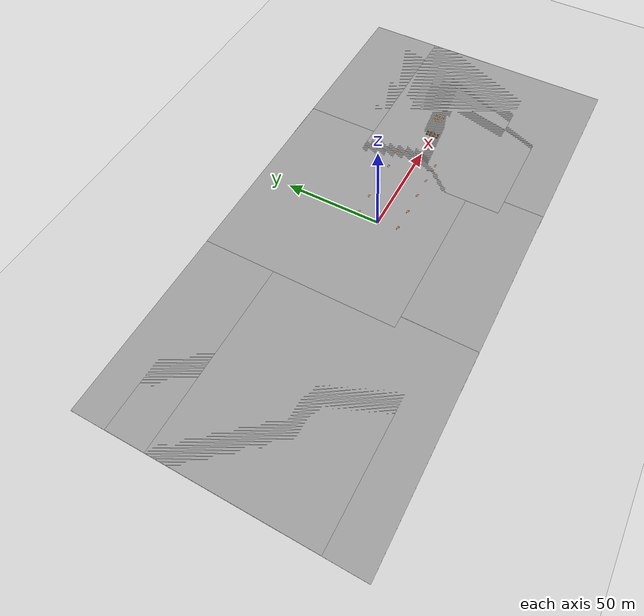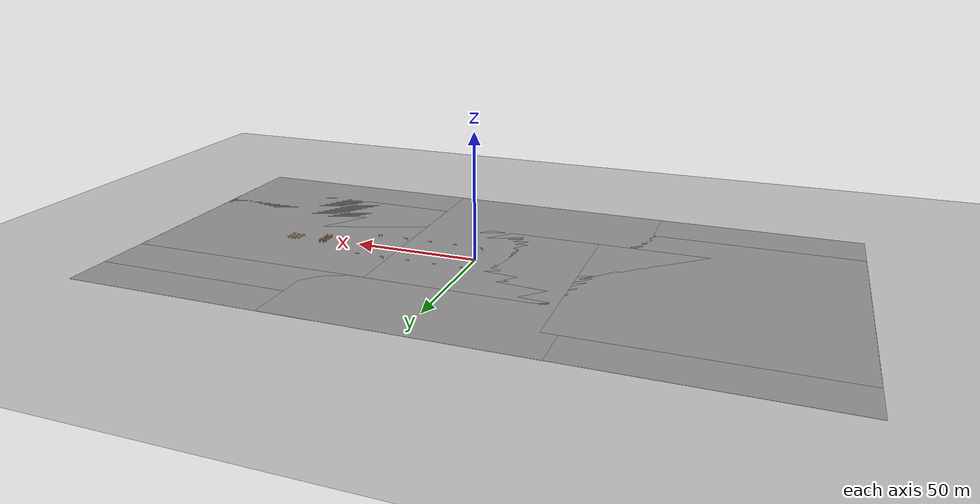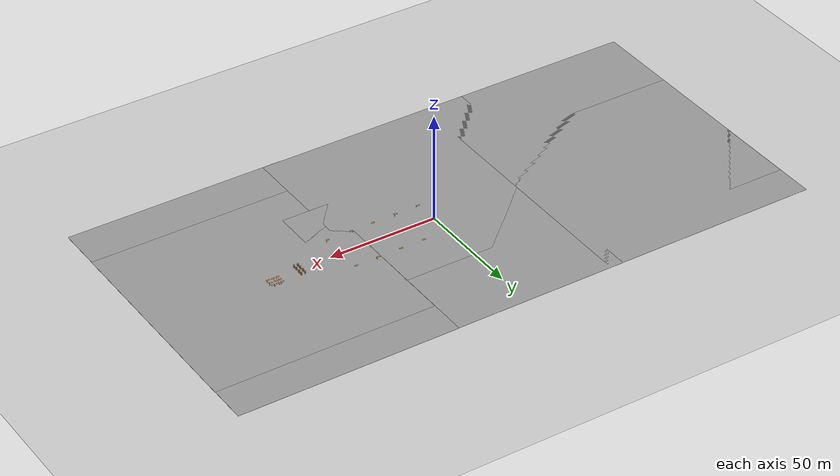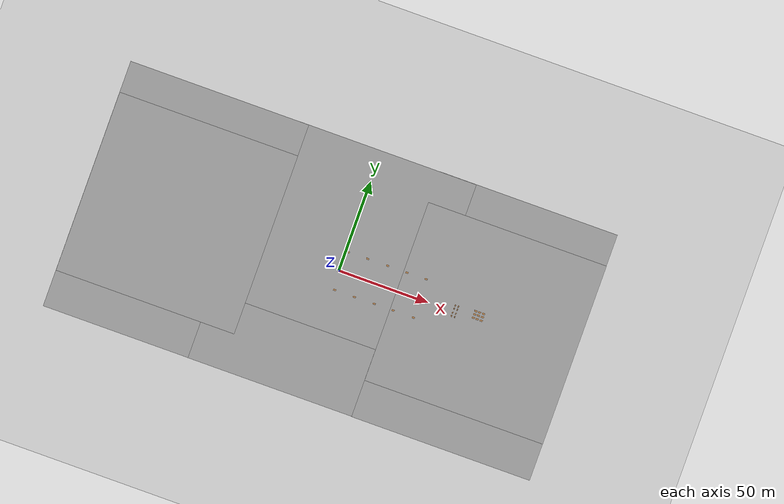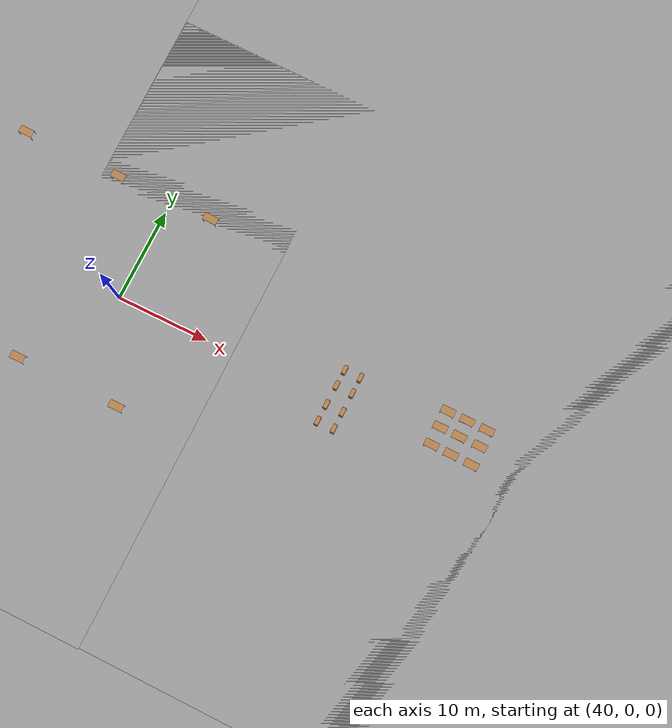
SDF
<sdf version="1.6">
 <world name="default">
  <light name="sun" type="directional">
   <pose>0 0 10 0 -0 0</pose>
   <diffuse>0.8 0.8 0.8 1</diffuse>
   <specular>0.2 0.2 0.2 1</specular>
   <attenuation>
    <range>1000</range>
    <constant>0.9</constant>
    <linear>0.01</linear>
    <quadratic>0.001</quadratic>
   </attenuation>
   <direction>-0.5 0.1 -0.9</direction>
  </light>
  <model name="ground_plane">
   <static>1</static>
   <link name="link">
    <collision name="collision">
     <geometry><plane><normal>0 0 1</normal><size>100 100</size></plane></geometry>
     <surface><friction><ode><mu>100</mu><mu2>50</mu2></ode></friction></surface>
    </collision>
    <visual name="visual">
     <cast_shadows>0</cast_shadows>
     <geometry><plane><normal>0 0 1</normal><size>100 100</size></plane></geometry>
     <material>
      <script><uri>file://media/materials/scripts/gazebo.material</uri><name>Gazebo/Grey</name></script>
     </material>
    </visual>
   </link>
  </model>
  <gravity>0 0 -9.8</gravity>
  <magnetic_field>6e-06 2.3e-05 -4.2e-05</magnetic_field>
  <atmosphere type="adiabatic"/>
  <physics name="default_physics" default="0" type="ode">
   <max_step_size>0.001</max_step_size>
   <real_time_factor>1</real_time_factor>
   <real_time_update_rate>1000</real_time_update_rate>
  </physics>
  <scene><ambient>0.4 0.4 0.4 1</ambient><background>0.7 0.7 0.7 1</background><shadows>1</shadows></scene>
  <audio><device>default</device></audio>
  <spherical_coordinates>
   <surface_model>EARTH_WGS84</surface_model>
   <latitude_deg>0</latitude_deg>
   <longitude_deg>0</longitude_deg>
   <elevation>0</elevation>
   <heading_deg>0</heading_deg>
  </spherical_coordinates>
  <model name="ground_plane_0">
   <static>1</static>
   <link name="link">
    <collision name="collision">
     <geometry><plane><normal>0 0 1</normal><size>100 100</size></plane></geometry>
     <surface><friction><ode><mu>100</mu><mu2>50</mu2></ode></friction></surface>
    </collision>
    <visual name="visual">
     <cast_shadows>0</cast_shadows>
     <geometry><plane><normal>0 0 1</normal><size>100 100</size></plane></geometry>
     <material>
      <script><uri>file://media/materials/scripts/gazebo.material</uri><name>Gazebo/Grey</name></script>
     </material>
    </visual>
   </link>
   <pose>-90.9597 -0.127631 0 0 -0 0</pose>
  </model>
  <model name="ground_plane_1">
   <static>1</static>
   <link name="link">
    <collision name="collision">
     <geometry><plane><normal>0 0 1</normal><size>100 100</size></plane></geometry>
     <surface><friction><ode><mu>100</mu><mu2>50</mu2></ode></friction></surface>
    </collision>
    <visual name="visual">
     <cast_shadows>0</cast_shadows>
     <geometry><plane><normal>0 0 1</normal><size>100 100</size></plane></geometry>
     <material>
      <script><uri>file://media/materials/scripts/gazebo.material</uri><name>Gazebo/Grey</name></script>
     </material>
    </visual>
   </link>
   <pose>82.2329 0.073563 0 0 -0 0</pose>
  </model>
  <model name="ground_plane_2">
   <static>1</static>
   <link name="link">
    <collision name="collision">
     <geometry><plane><normal>0 0 1</normal><size>100 100</size></plane></geometry>
     <surface><friction><ode><mu>100</mu><mu2>50</mu2></ode></friction></surface>
    </collision>
    <visual name="visual">
     <cast_shadows>0</cast_shadows>
     <geometry><plane><normal>0 0 1</normal><size>100 100</size></plane></geometry>
     <material>
      <script><uri>file://media/materials/scripts/gazebo.material</uri><name>Gazebo/Grey</name></script>
     </material>
    </visual>
   </link>
   <pose>-91.0464 17.2441 0 0 -0 0</pose>
  </model>
  <model name="ground_plane_3">
   <static>1</static>
   <link name="link">
    <collision name="collision">
     <geometry><plane><normal>0 0 1</normal><size>100 100</size></plane></geometry>
     <surface><friction><ode><mu>100</mu><mu2>50</mu2></ode></friction></surface>
    </collision>
    <visual name="visual">
     <cast_shadows>0</cast_shadows>
     <geometry><plane><normal>0 0 1</normal><size>100 100</size></plane></geometry>
     <material>
      <script><uri>file://media/materials/scripts/gazebo.material</uri><name>Gazebo/Grey</name></script>
     </material>
    </visual>
   </link>
   <pose>3.00219 17.3131 0 0 -0 0</pose>
  </model>
  <model name="ground_plane_4">
   <static>1</static>
   <link name="link">
    <collision name="collision">
     <geometry><plane><normal>0 0 1</normal><size>100 100</size></plane></geometry>
     <surface><friction><ode><mu>100</mu><mu2>50</mu2></ode></friction></surface>
    </collision>
    <visual name="visual">
     <cast_shadows>0</cast_shadows>
     <geometry><plane><normal>0 0 1</normal><size>100 100</size></plane></geometry>
     <material>
      <script><uri>file://media/materials/scripts/gazebo.material</uri><name>Gazebo/Grey</name></script>
     </material>
    </visual>
   </link>
   <pose>82.1286 17.4365 0 0 -0 0</pose>
  </model>
  <model name="ground_plane_5">
   <static>1</static>
   <link name="link">
    <collision name="collision">
     <geometry><plane><normal>0 0 1</normal><size>100 100</size></plane></geometry>
     <surface><friction><ode><mu>100</mu><mu2>50</mu2></ode></friction></surface>
    </collision>
    <visual name="visual">
     <cast_shadows>0</cast_shadows>
     <geometry><plane><normal>0 0 1</normal><size>100 100</size></plane></geometry>
     <material>
      <script><uri>file://media/materials/scripts/gazebo.material</uri><name>Gazebo/Grey</name></script>
     </material>
    </visual>
   </link>
   <pose>82.1805 -20.337 0 0 -0 0</pose>
  </model>
  <model name="ground_plane_6">
   <static>1</static>
   <link name="link">
    <collision name="collision">
     <geometry><plane><normal>0 0 1</normal><size>100 100</size></plane></geometry>
     <surface><friction><ode><mu>100</mu><mu2>50</mu2></ode></friction></surface>
    </collision>
    <visual name="visual">
     <cast_shadows>0</cast_shadows>
     <geometry><plane><normal>0 0 1</normal><size>100 100</size></plane></geometry>
     <material>
      <script><uri>file://media/materials/scripts/gazebo.material</uri><name>Gazebo/Grey</name></script>
     </material>
    </visual>
   </link>
   <pose>-9.72801 -20.1818 0 0 -0 0</pose>
  </model>
  <model name="ground_plane_7">
   <static>1</static>
   <link name="link">
    <collision name="collision">
     <geometry><plane><normal>0 0 1</normal><size>100 100</size></plane></geometry>
     <surface><friction><ode><mu>100</mu><mu2>50</mu2></ode></friction></surface>
    </collision>
    <visual name="visual">
     <cast_shadows>0</cast_shadows>
     <geometry><plane><normal>0 0 1</normal><size>100 100</size></plane></geometry>
     <material>
      <script><uri>file://media/materials/scripts/gazebo.material</uri><name>Gazebo/Grey</name></script>
     </material>
    </visual>
   </link>
   <pose>-91.017 -20.1275 0 0 -0 0</pose>
  </model>
  <model name="table">
   <static>1</static>
   <link name="link">
    <collision name="surface">
     <pose>0 0 1 0 -0 0</pose>
     <geometry><box><size>1.5 0.8 0.03</size></box></geometry>
     <surface><friction><ode><mu>0.6</mu><mu2>0.6</mu2></ode></friction></surface>
    </collision>
    <visual name="visual1">
     <pose>0 0 1 0 -0 0</pose>
     <geometry><box><size>1.5 0.8 0.03</size></box></geometry>
     <material>
      <script><uri>file://media/materials/scripts/gazebo.material</uri><name>Gazebo/Wood</name></script>
     </material>
    </visual>
    <collision name="front_left_leg">
     <pose>0.68 0.38 0.5 0 -0 0</pose>
     <geometry><cylinder><radius>0.02</radius><length>1</length></cylinder></geometry>
    </collision>
    <visual name="front_left_leg">
     <pose>0.68 0.38 0.5 0 -0 0</pose>
     <geometry><cylinder><radius>0.02</radius><length>1</length></cylinder></geometry>
     <material>
      <script><uri>file://media/materials/scripts/gazebo.material</uri><name>Gazebo/Grey</name></script>
     </material>
    </visual>
    <collision name="front_right_leg">
     <pose>0.68 -0.38 0.5 0 -0 0</pose>
     <geometry><cylinder><radius>0.02</radius><length>1</length></cylinder></geometry>
    </collision>
    <visual name="front_right_leg">
     <pose>0.68 -0.38 0.5 0 -0 0</pose>
     <geometry><cylinder><radius>0.02</radius><length>1</length></cylinder></geometry>
     <material>
      <script><uri>file://media/materials/scripts/gazebo.material</uri><name>Gazebo/Grey</name></script>
     </material>
    </visual>
    <collision name="back_right_leg">
     <pose>-0.68 -0.38 0.5 0 -0 0</pose>
     <geometry><cylinder><radius>0.02</radius><length>1</length></cylinder></geometry>
    </collision>
    <visual name="back_right_leg">
     <pose>-0.68 -0.38 0.5 0 -0 0</pose>
     <geometry><cylinder><radius>0.02</radius><length>1</length></cylinder></geometry>
     <material>
      <script><uri>file://media/materials/scripts/gazebo.material</uri><name>Gazebo/Grey</name></script>
     </material>
    </visual>
    <collision name="back_left_leg">
     <pose>-0.68 0.38 0.5 0 -0 0</pose>
     <geometry><cylinder><radius>0.02</radius><length>1</length></cylinder></geometry>
    </collision>
    <visual name="back_left_leg">
     <pose>-0.68 0.38 0.5 0 -0 0</pose>
     <geometry><cylinder><radius>0.02</radius><length>1</length></cylinder></geometry>
     <material>
      <script><uri>file://media/materials/scripts/gazebo.material</uri><name>Gazebo/Grey</name></script>
     </material>
    </visual>
   </link>
   <pose>1.22981 10.8822 0 0 -0 0</pose>
  </model>
  <model name="table_0">
   <static>1</static>
   <link name="link">
    <collision name="surface">
     <pose>0 0 1 0 -0 0</pose>
     <geometry><box><size>1.5 0.8 0.03</size></box></geometry>
     <surface><friction><ode><mu>0.6</mu><mu2>0.6</mu2></ode></friction></surface>
    </collision>
    <visual name="visual1">
     <pose>0 0 1 0 -0 0</pose>
     <geometry><box><size>1.5 0.8 0.03</size></box></geometry>
     <material>
      <script><uri>file://media/materials/scripts/gazebo.material</uri><name>Gazebo/Wood</name></script>
     </material>
    </visual>
    <collision name="front_left_leg">
     <pose>0.68 0.38 0.5 0 -0 0</pose>
     <geometry><cylinder><radius>0.02</radius><length>1</length></cylinder></geometry>
    </collision>
    <visual name="front_left_leg">
     <pose>0.68 0.38 0.5 0 -0 0</pose>
     <geometry><cylinder><radius>0.02</radius><length>1</length></cylinder></geometry>
     <material>
      <script><uri>file://media/materials/scripts/gazebo.material</uri><name>Gazebo/Grey</name></script>
     </material>
    </visual>
    <collision name="front_right_leg">
     <pose>0.68 -0.38 0.5 0 -0 0</pose>
     <geometry><cylinder><radius>0.02</radius><length>1</length></cylinder></geometry>
    </collision>
    <visual name="front_right_leg">
     <pose>0.68 -0.38 0.5 0 -0 0</pose>
     <geometry><cylinder><radius>0.02</radius><length>1</length></cylinder></geometry>
     <material>
      <script><uri>file://media/materials/scripts/gazebo.material</uri><name>Gazebo/Grey</name></script>
     </material>
    </visual>
    <collision name="back_right_leg">
     <pose>-0.68 -0.38 0.5 0 -0 0</pose>
     <geometry><cylinder><radius>0.02</radius><length>1</length></cylinder></geometry>
    </collision>
    <visual name="back_right_leg">
     <pose>-0.68 -0.38 0.5 0 -0 0</pose>
     <geometry><cylinder><radius>0.02</radius><length>1</length></cylinder></geometry>
     <material>
      <script><uri>file://media/materials/scripts/gazebo.material</uri><name>Gazebo/Grey</name></script>
     </material>
    </visual>
    <collision name="back_left_leg">
     <pose>-0.68 0.38 0.5 0 -0 0</pose>
     <geometry><cylinder><radius>0.02</radius><length>1</length></cylinder></geometry>
    </collision>
    <visual name="back_left_leg">
     <pose>-0.68 0.38 0.5 0 -0 0</pose>
     <geometry><cylinder><radius>0.02</radius><length>1</length></cylinder></geometry>
     <material>
      <script><uri>file://media/materials/scripts/gazebo.material</uri><name>Gazebo/Grey</name></script>
     </material>
    </visual>
   </link>
   <pose>12.1097 11.1001 0 0 -0 0</pose>
  </model>
  <model name="table_1">
   <static>1</static>
   <link name="link">
    <collision name="surface">
     <pose>0 0 1 0 -0 0</pose>
     <geometry><box><size>1.5 0.8 0.03</size></box></geometry>
     <surface><friction><ode><mu>0.6</mu><mu2>0.6</mu2></ode></friction></surface>
    </collision>
    <visual name="visual1">
     <pose>0 0 1 0 -0 0</pose>
     <geometry><box><size>1.5 0.8 0.03</size></box></geometry>
     <material>
      <script><uri>file://media/materials/scripts/gazebo.material</uri><name>Gazebo/Wood</name></script>
     </material>
    </visual>
    <collision name="front_left_leg">
     <pose>0.68 0.38 0.5 0 -0 0</pose>
     <geometry><cylinder><radius>0.02</radius><length>1</length></cylinder></geometry>
    </collision>
    <visual name="front_left_leg">
     <pose>0.68 0.38 0.5 0 -0 0</pose>
     <geometry><cylinder><radius>0.02</radius><length>1</length></cylinder></geometry>
     <material>
      <script><uri>file://media/materials/scripts/gazebo.material</uri><name>Gazebo/Grey</name></script>
     </material>
    </visual>
    <collision name="front_right_leg">
     <pose>0.68 -0.38 0.5 0 -0 0</pose>
     <geometry><cylinder><radius>0.02</radius><length>1</length></cylinder></geometry>
    </collision>
    <visual name="front_right_leg">
     <pose>0.68 -0.38 0.5 0 -0 0</pose>
     <geometry><cylinder><radius>0.02</radius><length>1</length></cylinder></geometry>
     <material>
      <script><uri>file://media/materials/scripts/gazebo.material</uri><name>Gazebo/Grey</name></script>
     </material>
    </visual>
    <collision name="back_right_leg">
     <pose>-0.68 -0.38 0.5 0 -0 0</pose>
     <geometry><cylinder><radius>0.02</radius><length>1</length></cylinder></geometry>
    </collision>
    <visual name="back_right_leg">
     <pose>-0.68 -0.38 0.5 0 -0 0</pose>
     <geometry><cylinder><radius>0.02</radius><length>1</length></cylinder></geometry>
     <material>
      <script><uri>file://media/materials/scripts/gazebo.material</uri><name>Gazebo/Grey</name></script>
     </material>
    </visual>
    <collision name="back_left_leg">
     <pose>-0.68 0.38 0.5 0 -0 0</pose>
     <geometry><cylinder><radius>0.02</radius><length>1</length></cylinder></geometry>
    </collision>
    <visual name="back_left_leg">
     <pose>-0.68 0.38 0.5 0 -0 0</pose>
     <geometry><cylinder><radius>0.02</radius><length>1</length></cylinder></geometry>
     <material>
      <script><uri>file://media/materials/scripts/gazebo.material</uri><name>Gazebo/Grey</name></script>
     </material>
    </visual>
   </link>
   <pose>23.1992 11.1847 0 0 -0 0</pose>
  </model>
  <model name="table_2">
   <static>1</static>
   <link name="link">
    <collision name="surface">
     <pose>0 0 1 0 -0 0</pose>
     <geometry><box><size>1.5 0.8 0.03</size></box></geometry>
     <surface><friction><ode><mu>0.6</mu><mu2>0.6</mu2></ode></friction></surface>
    </collision>
    <visual name="visual1">
     <pose>0 0 1 0 -0 0</pose>
     <geometry><box><size>1.5 0.8 0.03</size></box></geometry>
     <material>
      <script><uri>file://media/materials/scripts/gazebo.material</uri><name>Gazebo/Wood</name></script>
     </material>
    </visual>
    <collision name="front_left_leg">
     <pose>0.68 0.38 0.5 0 -0 0</pose>
     <geometry><cylinder><radius>0.02</radius><length>1</length></cylinder></geometry>
    </collision>
    <visual name="front_left_leg">
     <pose>0.68 0.38 0.5 0 -0 0</pose>
     <geometry><cylinder><radius>0.02</radius><length>1</length></cylinder></geometry>
     <material>
      <script><uri>file://media/materials/scripts/gazebo.material</uri><name>Gazebo/Grey</name></script>
     </material>
    </visual>
    <collision name="front_right_leg">
     <pose>0.68 -0.38 0.5 0 -0 0</pose>
     <geometry><cylinder><radius>0.02</radius><length>1</length></cylinder></geometry>
    </collision>
    <visual name="front_right_leg">
     <pose>0.68 -0.38 0.5 0 -0 0</pose>
     <geometry><cylinder><radius>0.02</radius><length>1</length></cylinder></geometry>
     <material>
      <script><uri>file://media/materials/scripts/gazebo.material</uri><name>Gazebo/Grey</name></script>
     </material>
    </visual>
    <collision name="back_right_leg">
     <pose>-0.68 -0.38 0.5 0 -0 0</pose>
     <geometry><cylinder><radius>0.02</radius><length>1</length></cylinder></geometry>
    </collision>
    <visual name="back_right_leg">
     <pose>-0.68 -0.38 0.5 0 -0 0</pose>
     <geometry><cylinder><radius>0.02</radius><length>1</length></cylinder></geometry>
     <material>
      <script><uri>file://media/materials/scripts/gazebo.material</uri><name>Gazebo/Grey</name></script>
     </material>
    </visual>
    <collision name="back_left_leg">
     <pose>-0.68 0.38 0.5 0 -0 0</pose>
     <geometry><cylinder><radius>0.02</radius><length>1</length></cylinder></geometry>
    </collision>
    <visual name="back_left_leg">
     <pose>-0.68 0.38 0.5 0 -0 0</pose>
     <geometry><cylinder><radius>0.02</radius><length>1</length></cylinder></geometry>
     <material>
      <script><uri>file://media/materials/scripts/gazebo.material</uri><name>Gazebo/Grey</name></script>
     </material>
    </visual>
   </link>
   <pose>34.0221 11.2254 0 0 -0 0</pose>
  </model>
  <model name="table_3">
   <static>1</static>
   <link name="link">
    <collision name="surface">
     <pose>0 0 1 0 -0 0</pose>
     <geometry><box><size>1.5 0.8 0.03</size></box></geometry>
     <surface><friction><ode><mu>0.6</mu><mu2>0.6</mu2></ode></friction></surface>
    </collision>
    <visual name="visual1">
     <pose>0 0 1 0 -0 0</pose>
     <geometry><box><size>1.5 0.8 0.03</size></box></geometry>
     <material>
      <script><uri>file://media/materials/scripts/gazebo.material</uri><name>Gazebo/Wood</name></script>
     </material>
    </visual>
    <collision name="front_left_leg">
     <pose>0.68 0.38 0.5 0 -0 0</pose>
     <geometry><cylinder><radius>0.02</radius><length>1</length></cylinder></geometry>
    </collision>
    <visual name="front_left_leg">
     <pose>0.68 0.38 0.5 0 -0 0</pose>
     <geometry><cylinder><radius>0.02</radius><length>1</length></cylinder></geometry>
     <material>
      <script><uri>file://media/materials/scripts/gazebo.material</uri><name>Gazebo/Grey</name></script>
     </material>
    </visual>
    <collision name="front_right_leg">
     <pose>0.68 -0.38 0.5 0 -0 0</pose>
     <geometry><cylinder><radius>0.02</radius><length>1</length></cylinder></geometry>
    </collision>
    <visual name="front_right_leg">
     <pose>0.68 -0.38 0.5 0 -0 0</pose>
     <geometry><cylinder><radius>0.02</radius><length>1</length></cylinder></geometry>
     <material>
      <script><uri>file://media/materials/scripts/gazebo.material</uri><name>Gazebo/Grey</name></script>
     </material>
    </visual>
    <collision name="back_right_leg">
     <pose>-0.68 -0.38 0.5 0 -0 0</pose>
     <geometry><cylinder><radius>0.02</radius><length>1</length></cylinder></geometry>
    </collision>
    <visual name="back_right_leg">
     <pose>-0.68 -0.38 0.5 0 -0 0</pose>
     <geometry><cylinder><radius>0.02</radius><length>1</length></cylinder></geometry>
     <material>
      <script><uri>file://media/materials/scripts/gazebo.material</uri><name>Gazebo/Grey</name></script>
     </material>
    </visual>
    <collision name="back_left_leg">
     <pose>-0.68 0.38 0.5 0 -0 0</pose>
     <geometry><cylinder><radius>0.02</radius><length>1</length></cylinder></geometry>
    </collision>
    <visual name="back_left_leg">
     <pose>-0.68 0.38 0.5 0 -0 0</pose>
     <geometry><cylinder><radius>0.02</radius><length>1</length></cylinder></geometry>
     <material>
      <script><uri>file://media/materials/scripts/gazebo.material</uri><name>Gazebo/Grey</name></script>
     </material>
    </visual>
   </link>
   <pose>44.6592 11.373 0 0 -0 0</pose>
  </model>
  <model name="table_4">
   <static>1</static>
   <link name="link">
    <collision name="surface">
     <pose>0 0 1 0 -0 0</pose>
     <geometry><box><size>1.5 0.8 0.03</size></box></geometry>
     <surface><friction><ode><mu>0.6</mu><mu2>0.6</mu2></ode></friction></surface>
    </collision>
    <visual name="visual1">
     <pose>0 0 1 0 -0 0</pose>
     <geometry><box><size>1.5 0.8 0.03</size></box></geometry>
     <material>
      <script><uri>file://media/materials/scripts/gazebo.material</uri><name>Gazebo/Wood</name></script>
     </material>
    </visual>
    <collision name="front_left_leg">
     <pose>0.68 0.38 0.5 0 -0 0</pose>
     <geometry><cylinder><radius>0.02</radius><length>1</length></cylinder></geometry>
    </collision>
    <visual name="front_left_leg">
     <pose>0.68 0.38 0.5 0 -0 0</pose>
     <geometry><cylinder><radius>0.02</radius><length>1</length></cylinder></geometry>
     <material>
      <script><uri>file://media/materials/scripts/gazebo.material</uri><name>Gazebo/Grey</name></script>
     </material>
    </visual>
    <collision name="front_right_leg">
     <pose>0.68 -0.38 0.5 0 -0 0</pose>
     <geometry><cylinder><radius>0.02</radius><length>1</length></cylinder></geometry>
    </collision>
    <visual name="front_right_leg">
     <pose>0.68 -0.38 0.5 0 -0 0</pose>
     <geometry><cylinder><radius>0.02</radius><length>1</length></cylinder></geometry>
     <material>
      <script><uri>file://media/materials/scripts/gazebo.material</uri><name>Gazebo/Grey</name></script>
     </material>
    </visual>
    <collision name="back_right_leg">
     <pose>-0.68 -0.38 0.5 0 -0 0</pose>
     <geometry><cylinder><radius>0.02</radius><length>1</length></cylinder></geometry>
    </collision>
    <visual name="back_right_leg">
     <pose>-0.68 -0.38 0.5 0 -0 0</pose>
     <geometry><cylinder><radius>0.02</radius><length>1</length></cylinder></geometry>
     <material>
      <script><uri>file://media/materials/scripts/gazebo.material</uri><name>Gazebo/Grey</name></script>
     </material>
    </visual>
    <collision name="back_left_leg">
     <pose>-0.68 0.38 0.5 0 -0 0</pose>
     <geometry><cylinder><radius>0.02</radius><length>1</length></cylinder></geometry>
    </collision>
    <visual name="back_left_leg">
     <pose>-0.68 0.38 0.5 0 -0 0</pose>
     <geometry><cylinder><radius>0.02</radius><length>1</length></cylinder></geometry>
     <material>
      <script><uri>file://media/materials/scripts/gazebo.material</uri><name>Gazebo/Grey</name></script>
     </material>
    </visual>
   </link>
   <pose>1.22037 -10.2887 0 0 -0 0</pose>
  </model>
  <model name="table_5">
   <static>1</static>
   <link name="link">
    <collision name="surface">
     <pose>0 0 1 0 -0 0</pose>
     <geometry><box><size>1.5 0.8 0.03</size></box></geometry>
     <surface><friction><ode><mu>0.6</mu><mu2>0.6</mu2></ode></friction></surface>
    </collision>
    <visual name="visual1">
     <pose>0 0 1 0 -0 0</pose>
     <geometry><box><size>1.5 0.8 0.03</size></box></geometry>
     <material>
      <script><uri>file://media/materials/scripts/gazebo.material</uri><name>Gazebo/Wood</name></script>
     </material>
    </visual>
    <collision name="front_left_leg">
     <pose>0.68 0.38 0.5 0 -0 0</pose>
     <geometry><cylinder><radius>0.02</radius><length>1</length></cylinder></geometry>
    </collision>
    <visual name="front_left_leg">
     <pose>0.68 0.38 0.5 0 -0 0</pose>
     <geometry><cylinder><radius>0.02</radius><length>1</length></cylinder></geometry>
     <material>
      <script><uri>file://media/materials/scripts/gazebo.material</uri><name>Gazebo/Grey</name></script>
     </material>
    </visual>
    <collision name="front_right_leg">
     <pose>0.68 -0.38 0.5 0 -0 0</pose>
     <geometry><cylinder><radius>0.02</radius><length>1</length></cylinder></geometry>
    </collision>
    <visual name="front_right_leg">
     <pose>0.68 -0.38 0.5 0 -0 0</pose>
     <geometry><cylinder><radius>0.02</radius><length>1</length></cylinder></geometry>
     <material>
      <script><uri>file://media/materials/scripts/gazebo.material</uri><name>Gazebo/Grey</name></script>
     </material>
    </visual>
    <collision name="back_right_leg">
     <pose>-0.68 -0.38 0.5 0 -0 0</pose>
     <geometry><cylinder><radius>0.02</radius><length>1</length></cylinder></geometry>
    </collision>
    <visual name="back_right_leg">
     <pose>-0.68 -0.38 0.5 0 -0 0</pose>
     <geometry><cylinder><radius>0.02</radius><length>1</length></cylinder></geometry>
     <material>
      <script><uri>file://media/materials/scripts/gazebo.material</uri><name>Gazebo/Grey</name></script>
     </material>
    </visual>
    <collision name="back_left_leg">
     <pose>-0.68 0.38 0.5 0 -0 0</pose>
     <geometry><cylinder><radius>0.02</radius><length>1</length></cylinder></geometry>
    </collision>
    <visual name="back_left_leg">
     <pose>-0.68 0.38 0.5 0 -0 0</pose>
     <geometry><cylinder><radius>0.02</radius><length>1</length></cylinder></geometry>
     <material>
      <script><uri>file://media/materials/scripts/gazebo.material</uri><name>Gazebo/Grey</name></script>
     </material>
    </visual>
   </link>
   <pose>12.2676 -10.281 0 0 -0 0</pose>
  </model>
  <model name="table_6">
   <static>1</static>
   <link name="link">
    <collision name="surface">
     <pose>0 0 1 0 -0 0</pose>
     <geometry><box><size>1.5 0.8 0.03</size></box></geometry>
     <surface><friction><ode><mu>0.6</mu><mu2>0.6</mu2></ode></friction></surface>
    </collision>
    <visual name="visual1">
     <pose>0 0 1 0 -0 0</pose>
     <geometry><box><size>1.5 0.8 0.03</size></box></geometry>
     <material>
      <script><uri>file://media/materials/scripts/gazebo.material</uri><name>Gazebo/Wood</name></script>
     </material>
    </visual>
    <collision name="front_left_leg">
     <pose>0.68 0.38 0.5 0 -0 0</pose>
     <geometry><cylinder><radius>0.02</radius><length>1</length></cylinder></geometry>
    </collision>
    <visual name="front_left_leg">
     <pose>0.68 0.38 0.5 0 -0 0</pose>
     <geometry><cylinder><radius>0.02</radius><length>1</length></cylinder></geometry>
     <material>
      <script><uri>file://media/materials/scripts/gazebo.material</uri><name>Gazebo/Grey</name></script>
     </material>
    </visual>
    <collision name="front_right_leg">
     <pose>0.68 -0.38 0.5 0 -0 0</pose>
     <geometry><cylinder><radius>0.02</radius><length>1</length></cylinder></geometry>
    </collision>
    <visual name="front_right_leg">
     <pose>0.68 -0.38 0.5 0 -0 0</pose>
     <geometry><cylinder><radius>0.02</radius><length>1</length></cylinder></geometry>
     <material>
      <script><uri>file://media/materials/scripts/gazebo.material</uri><name>Gazebo/Grey</name></script>
     </material>
    </visual>
    <collision name="back_right_leg">
     <pose>-0.68 -0.38 0.5 0 -0 0</pose>
     <geometry><cylinder><radius>0.02</radius><length>1</length></cylinder></geometry>
    </collision>
    <visual name="back_right_leg">
     <pose>-0.68 -0.38 0.5 0 -0 0</pose>
     <geometry><cylinder><radius>0.02</radius><length>1</length></cylinder></geometry>
     <material>
      <script><uri>file://media/materials/scripts/gazebo.material</uri><name>Gazebo/Grey</name></script>
     </material>
    </visual>
    <collision name="back_left_leg">
     <pose>-0.68 0.38 0.5 0 -0 0</pose>
     <geometry><cylinder><radius>0.02</radius><length>1</length></cylinder></geometry>
    </collision>
    <visual name="back_left_leg">
     <pose>-0.68 0.38 0.5 0 -0 0</pose>
     <geometry><cylinder><radius>0.02</radius><length>1</length></cylinder></geometry>
     <material>
      <script><uri>file://media/materials/scripts/gazebo.material</uri><name>Gazebo/Grey</name></script>
     </material>
    </visual>
   </link>
   <pose>23.3126 -10.121 0 0 -0 0</pose>
  </model>
  <model name="table_7">
   <static>1</static>
   <link name="link">
    <collision name="surface">
     <pose>0 0 1 0 -0 0</pose>
     <geometry><box><size>1.5 0.8 0.03</size></box></geometry>
     <surface><friction><ode><mu>0.6</mu><mu2>0.6</mu2></ode></friction></surface>
    </collision>
    <visual name="visual1">
     <pose>0 0 1 0 -0 0</pose>
     <geometry><box><size>1.5 0.8 0.03</size></box></geometry>
     <material>
      <script><uri>file://media/materials/scripts/gazebo.material</uri><name>Gazebo/Wood</name></script>
     </material>
    </visual>
    <collision name="front_left_leg">
     <pose>0.68 0.38 0.5 0 -0 0</pose>
     <geometry><cylinder><radius>0.02</radius><length>1</length></cylinder></geometry>
    </collision>
    <visual name="front_left_leg">
     <pose>0.68 0.38 0.5 0 -0 0</pose>
     <geometry><cylinder><radius>0.02</radius><length>1</length></cylinder></geometry>
     <material>
      <script><uri>file://media/materials/scripts/gazebo.material</uri><name>Gazebo/Grey</name></script>
     </material>
    </visual>
    <collision name="front_right_leg">
     <pose>0.68 -0.38 0.5 0 -0 0</pose>
     <geometry><cylinder><radius>0.02</radius><length>1</length></cylinder></geometry>
    </collision>
    <visual name="front_right_leg">
     <pose>0.68 -0.38 0.5 0 -0 0</pose>
     <geometry><cylinder><radius>0.02</radius><length>1</length></cylinder></geometry>
     <material>
      <script><uri>file://media/materials/scripts/gazebo.material</uri><name>Gazebo/Grey</name></script>
     </material>
    </visual>
    <collision name="back_right_leg">
     <pose>-0.68 -0.38 0.5 0 -0 0</pose>
     <geometry><cylinder><radius>0.02</radius><length>1</length></cylinder></geometry>
    </collision>
    <visual name="back_right_leg">
     <pose>-0.68 -0.38 0.5 0 -0 0</pose>
     <geometry><cylinder><radius>0.02</radius><length>1</length></cylinder></geometry>
     <material>
      <script><uri>file://media/materials/scripts/gazebo.material</uri><name>Gazebo/Grey</name></script>
     </material>
    </visual>
    <collision name="back_left_leg">
     <pose>-0.68 0.38 0.5 0 -0 0</pose>
     <geometry><cylinder><radius>0.02</radius><length>1</length></cylinder></geometry>
    </collision>
    <visual name="back_left_leg">
     <pose>-0.68 0.38 0.5 0 -0 0</pose>
     <geometry><cylinder><radius>0.02</radius><length>1</length></cylinder></geometry>
     <material>
      <script><uri>file://media/materials/scripts/gazebo.material</uri><name>Gazebo/Grey</name></script>
     </material>
    </visual>
   </link>
   <pose>33.9144 -10.0194 0 0 -0 0</pose>
  </model>
  <model name="table_8">
   <static>1</static>
   <link name="link">
    <collision name="surface">
     <pose>0 0 1 0 -0 0</pose>
     <geometry><box><size>1.5 0.8 0.03</size></box></geometry>
     <surface><friction><ode><mu>0.6</mu><mu2>0.6</mu2></ode></friction></surface>
    </collision>
    <visual name="visual1">
     <pose>0 0 1 0 -0 0</pose>
     <geometry><box><size>1.5 0.8 0.03</size></box></geometry>
     <material>
      <script><uri>file://media/materials/scripts/gazebo.material</uri><name>Gazebo/Wood</name></script>
     </material>
    </visual>
    <collision name="front_left_leg">
     <pose>0.68 0.38 0.5 0 -0 0</pose>
     <geometry><cylinder><radius>0.02</radius><length>1</length></cylinder></geometry>
    </collision>
    <visual name="front_left_leg">
     <pose>0.68 0.38 0.5 0 -0 0</pose>
     <geometry><cylinder><radius>0.02</radius><length>1</length></cylinder></geometry>
     <material>
      <script><uri>file://media/materials/scripts/gazebo.material</uri><name>Gazebo/Grey</name></script>
     </material>
    </visual>
    <collision name="front_right_leg">
     <pose>0.68 -0.38 0.5 0 -0 0</pose>
     <geometry><cylinder><radius>0.02</radius><length>1</length></cylinder></geometry>
    </collision>
    <visual name="front_right_leg">
     <pose>0.68 -0.38 0.5 0 -0 0</pose>
     <geometry><cylinder><radius>0.02</radius><length>1</length></cylinder></geometry>
     <material>
      <script><uri>file://media/materials/scripts/gazebo.material</uri><name>Gazebo/Grey</name></script>
     </material>
    </visual>
    <collision name="back_right_leg">
     <pose>-0.68 -0.38 0.5 0 -0 0</pose>
     <geometry><cylinder><radius>0.02</radius><length>1</length></cylinder></geometry>
    </collision>
    <visual name="back_right_leg">
     <pose>-0.68 -0.38 0.5 0 -0 0</pose>
     <geometry><cylinder><radius>0.02</radius><length>1</length></cylinder></geometry>
     <material>
      <script><uri>file://media/materials/scripts/gazebo.material</uri><name>Gazebo/Grey</name></script>
     </material>
    </visual>
    <collision name="back_left_leg">
     <pose>-0.68 0.38 0.5 0 -0 0</pose>
     <geometry><cylinder><radius>0.02</radius><length>1</length></cylinder></geometry>
    </collision>
    <visual name="back_left_leg">
     <pose>-0.68 0.38 0.5 0 -0 0</pose>
     <geometry><cylinder><radius>0.02</radius><length>1</length></cylinder></geometry>
     <material>
      <script><uri>file://media/materials/scripts/gazebo.material</uri><name>Gazebo/Grey</name></script>
     </material>
    </visual>
   </link>
   <pose>45.1523 -10.0078 0 0 -0 0</pose>
  </model>
  <model name="table_9">
   <static>1</static>
   <link name="link">
    <collision name="surface">
     <pose>0 0 1 0 -0 0</pose>
     <geometry><box><size>1.5 0.8 0.03</size></box></geometry>
     <surface><friction><ode><mu>0.6</mu><mu2>0.6</mu2></ode></friction></surface>
    </collision>
    <visual name="visual1">
     <pose>0 0 1 0 -0 0</pose>
     <geometry><box><size>1.5 0.8 0.03</size></box></geometry>
     <material>
      <script><uri>file://media/materials/scripts/gazebo.material</uri><name>Gazebo/Wood</name></script>
     </material>
    </visual>
    <collision name="front_left_leg">
     <pose>0.68 0.38 0.5 0 -0 0</pose>
     <geometry><cylinder><radius>0.02</radius><length>1</length></cylinder></geometry>
    </collision>
    <visual name="front_left_leg">
     <pose>0.68 0.38 0.5 0 -0 0</pose>
     <geometry><cylinder><radius>0.02</radius><length>1</length></cylinder></geometry>
     <material>
      <script><uri>file://media/materials/scripts/gazebo.material</uri><name>Gazebo/Grey</name></script>
     </material>
    </visual>
    <collision name="front_right_leg">
     <pose>0.68 -0.38 0.5 0 -0 0</pose>
     <geometry><cylinder><radius>0.02</radius><length>1</length></cylinder></geometry>
    </collision>
    <visual name="front_right_leg">
     <pose>0.68 -0.38 0.5 0 -0 0</pose>
     <geometry><cylinder><radius>0.02</radius><length>1</length></cylinder></geometry>
     <material>
      <script><uri>file://media/materials/scripts/gazebo.material</uri><name>Gazebo/Grey</name></script>
     </material>
    </visual>
    <collision name="back_right_leg">
     <pose>-0.68 -0.38 0.5 0 -0 0</pose>
     <geometry><cylinder><radius>0.02</radius><length>1</length></cylinder></geometry>
    </collision>
    <visual name="back_right_leg">
     <pose>-0.68 -0.38 0.5 0 -0 0</pose>
     <geometry><cylinder><radius>0.02</radius><length>1</length></cylinder></geometry>
     <material>
      <script><uri>file://media/materials/scripts/gazebo.material</uri><name>Gazebo/Grey</name></script>
     </material>
    </visual>
    <collision name="back_left_leg">
     <pose>-0.68 0.38 0.5 0 -0 0</pose>
     <geometry><cylinder><radius>0.02</radius><length>1</length></cylinder></geometry>
    </collision>
    <visual name="back_left_leg">
     <pose>-0.68 0.38 0.5 0 -0 0</pose>
     <geometry><cylinder><radius>0.02</radius><length>1</length></cylinder></geometry>
     <material>
      <script><uri>file://media/materials/scripts/gazebo.material</uri><name>Gazebo/Grey</name></script>
     </material>
    </visual>
   </link>
   <pose>75.0941 4.3048 0 0 -0 0</pose>
  </model>
  <model name="table_10">
   <static>1</static>
   <link name="link">
    <collision name="surface">
     <pose>0 0 1 0 -0 0</pose>
     <geometry><box><size>1.5 0.8 0.03</size></box></geometry>
     <surface><friction><ode><mu>0.6</mu><mu2>0.6</mu2></ode></friction></surface>
    </collision>
    <visual name="visual1">
     <pose>0 0 1 0 -0 0</pose>
     <geometry><box><size>1.5 0.8 0.03</size></box></geometry>
     <material>
      <script><uri>file://media/materials/scripts/gazebo.material</uri><name>Gazebo/Wood</name></script>
     </material>
    </visual>
    <collision name="front_left_leg">
     <pose>0.68 0.38 0.5 0 -0 0</pose>
     <geometry><cylinder><radius>0.02</radius><length>1</length></cylinder></geometry>
    </collision>
    <visual name="front_left_leg">
     <pose>0.68 0.38 0.5 0 -0 0</pose>
     <geometry><cylinder><radius>0.02</radius><length>1</length></cylinder></geometry>
     <material>
      <script><uri>file://media/materials/scripts/gazebo.material</uri><name>Gazebo/Grey</name></script>
     </material>
    </visual>
    <collision name="front_right_leg">
     <pose>0.68 -0.38 0.5 0 -0 0</pose>
     <geometry><cylinder><radius>0.02</radius><length>1</length></cylinder></geometry>
    </collision>
    <visual name="front_right_leg">
     <pose>0.68 -0.38 0.5 0 -0 0</pose>
     <geometry><cylinder><radius>0.02</radius><length>1</length></cylinder></geometry>
     <material>
      <script><uri>file://media/materials/scripts/gazebo.material</uri><name>Gazebo/Grey</name></script>
     </material>
    </visual>
    <collision name="back_right_leg">
     <pose>-0.68 -0.38 0.5 0 -0 0</pose>
     <geometry><cylinder><radius>0.02</radius><length>1</length></cylinder></geometry>
    </collision>
    <visual name="back_right_leg">
     <pose>-0.68 -0.38 0.5 0 -0 0</pose>
     <geometry><cylinder><radius>0.02</radius><length>1</length></cylinder></geometry>
     <material>
      <script><uri>file://media/materials/scripts/gazebo.material</uri><name>Gazebo/Grey</name></script>
     </material>
    </visual>
    <collision name="back_left_leg">
     <pose>-0.68 0.38 0.5 0 -0 0</pose>
     <geometry><cylinder><radius>0.02</radius><length>1</length></cylinder></geometry>
    </collision>
    <visual name="back_left_leg">
     <pose>-0.68 0.38 0.5 0 -0 0</pose>
     <geometry><cylinder><radius>0.02</radius><length>1</length></cylinder></geometry>
     <material>
      <script><uri>file://media/materials/scripts/gazebo.material</uri><name>Gazebo/Grey</name></script>
     </material>
    </visual>
   </link>
   <pose>77.2089 4.30261 0 0 -0 0</pose>
  </model>
  <model name="table_11">
   <static>1</static>
   <link name="link">
    <collision name="surface">
     <pose>0 0 1 0 -0 0</pose>
     <geometry><box><size>1.5 0.8 0.03</size></box></geometry>
     <surface><friction><ode><mu>0.6</mu><mu2>0.6</mu2></ode></friction></surface>
    </collision>
    <visual name="visual1">
     <pose>0 0 1 0 -0 0</pose>
     <geometry><box><size>1.5 0.8 0.03</size></box></geometry>
     <material>
      <script><uri>file://media/materials/scripts/gazebo.material</uri><name>Gazebo/Wood</name></script>
     </material>
    </visual>
    <collision name="front_left_leg">
     <pose>0.68 0.38 0.5 0 -0 0</pose>
     <geometry><cylinder><radius>0.02</radius><length>1</length></cylinder></geometry>
    </collision>
    <visual name="front_left_leg">
     <pose>0.68 0.38 0.5 0 -0 0</pose>
     <geometry><cylinder><radius>0.02</radius><length>1</length></cylinder></geometry>
     <material>
      <script><uri>file://media/materials/scripts/gazebo.material</uri><name>Gazebo/Grey</name></script>
     </material>
    </visual>
    <collision name="front_right_leg">
     <pose>0.68 -0.38 0.5 0 -0 0</pose>
     <geometry><cylinder><radius>0.02</radius><length>1</length></cylinder></geometry>
    </collision>
    <visual name="front_right_leg">
     <pose>0.68 -0.38 0.5 0 -0 0</pose>
     <geometry><cylinder><radius>0.02</radius><length>1</length></cylinder></geometry>
     <material>
      <script><uri>file://media/materials/scripts/gazebo.material</uri><name>Gazebo/Grey</name></script>
     </material>
    </visual>
    <collision name="back_right_leg">
     <pose>-0.68 -0.38 0.5 0 -0 0</pose>
     <geometry><cylinder><radius>0.02</radius><length>1</length></cylinder></geometry>
    </collision>
    <visual name="back_right_leg">
     <pose>-0.68 -0.38 0.5 0 -0 0</pose>
     <geometry><cylinder><radius>0.02</radius><length>1</length></cylinder></geometry>
     <material>
      <script><uri>file://media/materials/scripts/gazebo.material</uri><name>Gazebo/Grey</name></script>
     </material>
    </visual>
    <collision name="back_left_leg">
     <pose>-0.68 0.38 0.5 0 -0 0</pose>
     <geometry><cylinder><radius>0.02</radius><length>1</length></cylinder></geometry>
    </collision>
    <visual name="back_left_leg">
     <pose>-0.68 0.38 0.5 0 -0 0</pose>
     <geometry><cylinder><radius>0.02</radius><length>1</length></cylinder></geometry>
     <material>
      <script><uri>file://media/materials/scripts/gazebo.material</uri><name>Gazebo/Grey</name></script>
     </material>
    </visual>
   </link>
   <pose>79.3839 4.30475 0 0 -0 0</pose>
  </model>
  <model name="table_12">
   <static>1</static>
   <link name="link">
    <collision name="surface">
     <pose>0 0 1 0 -0 0</pose>
     <geometry><box><size>1.5 0.8 0.03</size></box></geometry>
     <surface><friction><ode><mu>0.6</mu><mu2>0.6</mu2></ode></friction></surface>
    </collision>
    <visual name="visual1">
     <pose>0 0 1 0 -0 0</pose>
     <geometry><box><size>1.5 0.8 0.03</size></box></geometry>
     <material>
      <script><uri>file://media/materials/scripts/gazebo.material</uri><name>Gazebo/Wood</name></script>
     </material>
    </visual>
    <collision name="front_left_leg">
     <pose>0.68 0.38 0.5 0 -0 0</pose>
     <geometry><cylinder><radius>0.02</radius><length>1</length></cylinder></geometry>
    </collision>
    <visual name="front_left_leg">
     <pose>0.68 0.38 0.5 0 -0 0</pose>
     <geometry><cylinder><radius>0.02</radius><length>1</length></cylinder></geometry>
     <material>
      <script><uri>file://media/materials/scripts/gazebo.material</uri><name>Gazebo/Grey</name></script>
     </material>
    </visual>
    <collision name="front_right_leg">
     <pose>0.68 -0.38 0.5 0 -0 0</pose>
     <geometry><cylinder><radius>0.02</radius><length>1</length></cylinder></geometry>
    </collision>
    <visual name="front_right_leg">
     <pose>0.68 -0.38 0.5 0 -0 0</pose>
     <geometry><cylinder><radius>0.02</radius><length>1</length></cylinder></geometry>
     <material>
      <script><uri>file://media/materials/scripts/gazebo.material</uri><name>Gazebo/Grey</name></script>
     </material>
    </visual>
    <collision name="back_right_leg">
     <pose>-0.68 -0.38 0.5 0 -0 0</pose>
     <geometry><cylinder><radius>0.02</radius><length>1</length></cylinder></geometry>
    </collision>
    <visual name="back_right_leg">
     <pose>-0.68 -0.38 0.5 0 -0 0</pose>
     <geometry><cylinder><radius>0.02</radius><length>1</length></cylinder></geometry>
     <material>
      <script><uri>file://media/materials/scripts/gazebo.material</uri><name>Gazebo/Grey</name></script>
     </material>
    </visual>
    <collision name="back_left_leg">
     <pose>-0.68 0.38 0.5 0 -0 0</pose>
     <geometry><cylinder><radius>0.02</radius><length>1</length></cylinder></geometry>
    </collision>
    <visual name="back_left_leg">
     <pose>-0.68 0.38 0.5 0 -0 0</pose>
     <geometry><cylinder><radius>0.02</radius><length>1</length></cylinder></geometry>
     <material>
      <script><uri>file://media/materials/scripts/gazebo.material</uri><name>Gazebo/Grey</name></script>
     </material>
    </visual>
   </link>
   <pose>75.0834 2.51521 0 0 -0 0</pose>
  </model>
  <model name="table_13">
   <static>1</static>
   <link name="link">
    <collision name="surface">
     <pose>0 0 1 0 -0 0</pose>
     <geometry><box><size>1.5 0.8 0.03</size></box></geometry>
     <surface><friction><ode><mu>0.6</mu><mu2>0.6</mu2></ode></friction></surface>
    </collision>
    <visual name="visual1">
     <pose>0 0 1 0 -0 0</pose>
     <geometry><box><size>1.5 0.8 0.03</size></box></geometry>
     <material>
      <script><uri>file://media/materials/scripts/gazebo.material</uri><name>Gazebo/Wood</name></script>
     </material>
    </visual>
    <collision name="front_left_leg">
     <pose>0.68 0.38 0.5 0 -0 0</pose>
     <geometry><cylinder><radius>0.02</radius><length>1</length></cylinder></geometry>
    </collision>
    <visual name="front_left_leg">
     <pose>0.68 0.38 0.5 0 -0 0</pose>
     <geometry><cylinder><radius>0.02</radius><length>1</length></cylinder></geometry>
     <material>
      <script><uri>file://media/materials/scripts/gazebo.material</uri><name>Gazebo/Grey</name></script>
     </material>
    </visual>
    <collision name="front_right_leg">
     <pose>0.68 -0.38 0.5 0 -0 0</pose>
     <geometry><cylinder><radius>0.02</radius><length>1</length></cylinder></geometry>
    </collision>
    <visual name="front_right_leg">
     <pose>0.68 -0.38 0.5 0 -0 0</pose>
     <geometry><cylinder><radius>0.02</radius><length>1</length></cylinder></geometry>
     <material>
      <script><uri>file://media/materials/scripts/gazebo.material</uri><name>Gazebo/Grey</name></script>
     </material>
    </visual>
    <collision name="back_right_leg">
     <pose>-0.68 -0.38 0.5 0 -0 0</pose>
     <geometry><cylinder><radius>0.02</radius><length>1</length></cylinder></geometry>
    </collision>
    <visual name="back_right_leg">
     <pose>-0.68 -0.38 0.5 0 -0 0</pose>
     <geometry><cylinder><radius>0.02</radius><length>1</length></cylinder></geometry>
     <material>
      <script><uri>file://media/materials/scripts/gazebo.material</uri><name>Gazebo/Grey</name></script>
     </material>
    </visual>
    <collision name="back_left_leg">
     <pose>-0.68 0.38 0.5 0 -0 0</pose>
     <geometry><cylinder><radius>0.02</radius><length>1</length></cylinder></geometry>
    </collision>
    <visual name="back_left_leg">
     <pose>-0.68 0.38 0.5 0 -0 0</pose>
     <geometry><cylinder><radius>0.02</radius><length>1</length></cylinder></geometry>
     <material>
      <script><uri>file://media/materials/scripts/gazebo.material</uri><name>Gazebo/Grey</name></script>
     </material>
    </visual>
   </link>
   <pose>77.1799 2.51562 0 0 -0 0</pose>
  </model>
  <model name="table_14">
   <static>1</static>
   <link name="link">
    <collision name="surface">
     <pose>0 0 1 0 -0 0</pose>
     <geometry><box><size>1.5 0.8 0.03</size></box></geometry>
     <surface><friction><ode><mu>0.6</mu><mu2>0.6</mu2></ode></friction></surface>
    </collision>
    <visual name="visual1">
     <pose>0 0 1 0 -0 0</pose>
     <geometry><box><size>1.5 0.8 0.03</size></box></geometry>
     <material>
      <script><uri>file://media/materials/scripts/gazebo.material</uri><name>Gazebo/Wood</name></script>
     </material>
    </visual>
    <collision name="front_left_leg">
     <pose>0.68 0.38 0.5 0 -0 0</pose>
     <geometry><cylinder><radius>0.02</radius><length>1</length></cylinder></geometry>
    </collision>
    <visual name="front_left_leg">
     <pose>0.68 0.38 0.5 0 -0 0</pose>
     <geometry><cylinder><radius>0.02</radius><length>1</length></cylinder></geometry>
     <material>
      <script><uri>file://media/materials/scripts/gazebo.material</uri><name>Gazebo/Grey</name></script>
     </material>
    </visual>
    <collision name="front_right_leg">
     <pose>0.68 -0.38 0.5 0 -0 0</pose>
     <geometry><cylinder><radius>0.02</radius><length>1</length></cylinder></geometry>
    </collision>
    <visual name="front_right_leg">
     <pose>0.68 -0.38 0.5 0 -0 0</pose>
     <geometry><cylinder><radius>0.02</radius><length>1</length></cylinder></geometry>
     <material>
      <script><uri>file://media/materials/scripts/gazebo.material</uri><name>Gazebo/Grey</name></script>
     </material>
    </visual>
    <collision name="back_right_leg">
     <pose>-0.68 -0.38 0.5 0 -0 0</pose>
     <geometry><cylinder><radius>0.02</radius><length>1</length></cylinder></geometry>
    </collision>
    <visual name="back_right_leg">
     <pose>-0.68 -0.38 0.5 0 -0 0</pose>
     <geometry><cylinder><radius>0.02</radius><length>1</length></cylinder></geometry>
     <material>
      <script><uri>file://media/materials/scripts/gazebo.material</uri><name>Gazebo/Grey</name></script>
     </material>
    </visual>
    <collision name="back_left_leg">
     <pose>-0.68 0.38 0.5 0 -0 0</pose>
     <geometry><cylinder><radius>0.02</radius><length>1</length></cylinder></geometry>
    </collision>
    <visual name="back_left_leg">
     <pose>-0.68 0.38 0.5 0 -0 0</pose>
     <geometry><cylinder><radius>0.02</radius><length>1</length></cylinder></geometry>
     <material>
      <script><uri>file://media/materials/scripts/gazebo.material</uri><name>Gazebo/Grey</name></script>
     </material>
    </visual>
   </link>
   <pose>79.4209 2.54135 0 0 -0 0</pose>
  </model>
  <model name="table_15">
   <static>1</static>
   <link name="link">
    <collision name="surface">
     <pose>0 0 1 0 -0 0</pose>
     <geometry><box><size>1.5 0.8 0.03</size></box></geometry>
     <surface><friction><ode><mu>0.6</mu><mu2>0.6</mu2></ode></friction></surface>
    </collision>
    <visual name="visual1">
     <pose>0 0 1 0 -0 0</pose>
     <geometry><box><size>1.5 0.8 0.03</size></box></geometry>
     <material>
      <script><uri>file://media/materials/scripts/gazebo.material</uri><name>Gazebo/Wood</name></script>
     </material>
    </visual>
    <collision name="front_left_leg">
     <pose>0.68 0.38 0.5 0 -0 0</pose>
     <geometry><cylinder><radius>0.02</radius><length>1</length></cylinder></geometry>
    </collision>
    <visual name="front_left_leg">
     <pose>0.68 0.38 0.5 0 -0 0</pose>
     <geometry><cylinder><radius>0.02</radius><length>1</length></cylinder></geometry>
     <material>
      <script><uri>file://media/materials/scripts/gazebo.material</uri><name>Gazebo/Grey</name></script>
     </material>
    </visual>
    <collision name="front_right_leg">
     <pose>0.68 -0.38 0.5 0 -0 0</pose>
     <geometry><cylinder><radius>0.02</radius><length>1</length></cylinder></geometry>
    </collision>
    <visual name="front_right_leg">
     <pose>0.68 -0.38 0.5 0 -0 0</pose>
     <geometry><cylinder><radius>0.02</radius><length>1</length></cylinder></geometry>
     <material>
      <script><uri>file://media/materials/scripts/gazebo.material</uri><name>Gazebo/Grey</name></script>
     </material>
    </visual>
    <collision name="back_right_leg">
     <pose>-0.68 -0.38 0.5 0 -0 0</pose>
     <geometry><cylinder><radius>0.02</radius><length>1</length></cylinder></geometry>
    </collision>
    <visual name="back_right_leg">
     <pose>-0.68 -0.38 0.5 0 -0 0</pose>
     <geometry><cylinder><radius>0.02</radius><length>1</length></cylinder></geometry>
     <material>
      <script><uri>file://media/materials/scripts/gazebo.material</uri><name>Gazebo/Grey</name></script>
     </material>
    </visual>
    <collision name="back_left_leg">
     <pose>-0.68 0.38 0.5 0 -0 0</pose>
     <geometry><cylinder><radius>0.02</radius><length>1</length></cylinder></geometry>
    </collision>
    <visual name="back_left_leg">
     <pose>-0.68 0.38 0.5 0 -0 0</pose>
     <geometry><cylinder><radius>0.02</radius><length>1</length></cylinder></geometry>
     <material>
      <script><uri>file://media/materials/scripts/gazebo.material</uri><name>Gazebo/Grey</name></script>
     </material>
    </visual>
   </link>
   <pose>75.0589 0.573461 0 0 -0 0</pose>
  </model>
  <model name="table_16">
   <static>1</static>
   <link name="link">
    <collision name="surface">
     <pose>0 0 1 0 -0 0</pose>
     <geometry><box><size>1.5 0.8 0.03</size></box></geometry>
     <surface><friction><ode><mu>0.6</mu><mu2>0.6</mu2></ode></friction></surface>
    </collision>
    <visual name="visual1">
     <pose>0 0 1 0 -0 0</pose>
     <geometry><box><size>1.5 0.8 0.03</size></box></geometry>
     <material>
      <script><uri>file://media/materials/scripts/gazebo.material</uri><name>Gazebo/Wood</name></script>
     </material>
    </visual>
    <collision name="front_left_leg">
     <pose>0.68 0.38 0.5 0 -0 0</pose>
     <geometry><cylinder><radius>0.02</radius><length>1</length></cylinder></geometry>
    </collision>
    <visual name="front_left_leg">
     <pose>0.68 0.38 0.5 0 -0 0</pose>
     <geometry><cylinder><radius>0.02</radius><length>1</length></cylinder></geometry>
     <material>
      <script><uri>file://media/materials/scripts/gazebo.material</uri><name>Gazebo/Grey</name></script>
     </material>
    </visual>
    <collision name="front_right_leg">
     <pose>0.68 -0.38 0.5 0 -0 0</pose>
     <geometry><cylinder><radius>0.02</radius><length>1</length></cylinder></geometry>
    </collision>
    <visual name="front_right_leg">
     <pose>0.68 -0.38 0.5 0 -0 0</pose>
     <geometry><cylinder><radius>0.02</radius><length>1</length></cylinder></geometry>
     <material>
      <script><uri>file://media/materials/scripts/gazebo.material</uri><name>Gazebo/Grey</name></script>
     </material>
    </visual>
    <collision name="back_right_leg">
     <pose>-0.68 -0.38 0.5 0 -0 0</pose>
     <geometry><cylinder><radius>0.02</radius><length>1</length></cylinder></geometry>
    </collision>
    <visual name="back_right_leg">
     <pose>-0.68 -0.38 0.5 0 -0 0</pose>
     <geometry><cylinder><radius>0.02</radius><length>1</length></cylinder></geometry>
     <material>
      <script><uri>file://media/materials/scripts/gazebo.material</uri><name>Gazebo/Grey</name></script>
     </material>
    </visual>
    <collision name="back_left_leg">
     <pose>-0.68 0.38 0.5 0 -0 0</pose>
     <geometry><cylinder><radius>0.02</radius><length>1</length></cylinder></geometry>
    </collision>
    <visual name="back_left_leg">
     <pose>-0.68 0.38 0.5 0 -0 0</pose>
     <geometry><cylinder><radius>0.02</radius><length>1</length></cylinder></geometry>
     <material>
      <script><uri>file://media/materials/scripts/gazebo.material</uri><name>Gazebo/Grey</name></script>
     </material>
    </visual>
   </link>
   <pose>77.2118 0.552939 0 0 -0 0</pose>
  </model>
  <model name="table_17">
   <static>1</static>
   <link name="link">
    <collision name="surface">
     <pose>0 0 1 0 -0 0</pose>
     <geometry><box><size>1.5 0.8 0.03</size></box></geometry>
     <surface><friction><ode><mu>0.6</mu><mu2>0.6</mu2></ode></friction></surface>
    </collision>
    <visual name="visual1">
     <pose>0 0 1 0 -0 0</pose>
     <geometry><box><size>1.5 0.8 0.03</size></box></geometry>
     <material>
      <script><uri>file://media/materials/scripts/gazebo.material</uri><name>Gazebo/Wood</name></script>
     </material>
    </visual>
    <collision name="front_left_leg">
     <pose>0.68 0.38 0.5 0 -0 0</pose>
     <geometry><cylinder><radius>0.02</radius><length>1</length></cylinder></geometry>
    </collision>
    <visual name="front_left_leg">
     <pose>0.68 0.38 0.5 0 -0 0</pose>
     <geometry><cylinder><radius>0.02</radius><length>1</length></cylinder></geometry>
     <material>
      <script><uri>file://media/materials/scripts/gazebo.material</uri><name>Gazebo/Grey</name></script>
     </material>
    </visual>
    <collision name="front_right_leg">
     <pose>0.68 -0.38 0.5 0 -0 0</pose>
     <geometry><cylinder><radius>0.02</radius><length>1</length></cylinder></geometry>
    </collision>
    <visual name="front_right_leg">
     <pose>0.68 -0.38 0.5 0 -0 0</pose>
     <geometry><cylinder><radius>0.02</radius><length>1</length></cylinder></geometry>
     <material>
      <script><uri>file://media/materials/scripts/gazebo.material</uri><name>Gazebo/Grey</name></script>
     </material>
    </visual>
    <collision name="back_right_leg">
     <pose>-0.68 -0.38 0.5 0 -0 0</pose>
     <geometry><cylinder><radius>0.02</radius><length>1</length></cylinder></geometry>
    </collision>
    <visual name="back_right_leg">
     <pose>-0.68 -0.38 0.5 0 -0 0</pose>
     <geometry><cylinder><radius>0.02</radius><length>1</length></cylinder></geometry>
     <material>
      <script><uri>file://media/materials/scripts/gazebo.material</uri><name>Gazebo/Grey</name></script>
     </material>
    </visual>
    <collision name="back_left_leg">
     <pose>-0.68 0.38 0.5 0 -0 0</pose>
     <geometry><cylinder><radius>0.02</radius><length>1</length></cylinder></geometry>
    </collision>
    <visual name="back_left_leg">
     <pose>-0.68 0.38 0.5 0 -0 0</pose>
     <geometry><cylinder><radius>0.02</radius><length>1</length></cylinder></geometry>
     <material>
      <script><uri>file://media/materials/scripts/gazebo.material</uri><name>Gazebo/Grey</name></script>
     </material>
    </visual>
   </link>
   <pose>79.4525 0.512163 0 0 -0 0</pose>
  </model>
  <model name="bookshelf">
   <static>1</static>
   <link name="link">
    <inertial><mass>1</mass></inertial>
    <collision name="back">
     <pose>0 0.005 0.6 0 -0 0</pose>
     <geometry><box><size>0.9 0.01 1.2</size></box></geometry>
    </collision>
    <visual name="visual1">
     <pose>0 0.005 0.6 0 -0 0</pose>
     <geometry><box><size>0.9 0.01 1.2</size></box></geometry>
     <material>
      <script><uri>file://media/materials/scripts/gazebo.material</uri><name>Gazebo/Wood</name></script>
     </material>
    </visual>
    <collision name="left_side">
     <pose>0.45 -0.195 0.6 0 -0 0</pose>
     <geometry><box><size>0.02 0.4 1.2</size></box></geometry>
    </collision>
    <visual name="visual2">
     <pose>0.45 -0.195 0.6 0 -0 0</pose>
     <geometry><box><size>0.02 0.4 1.2</size></box></geometry>
     <material>
      <script><uri>file://media/materials/scripts/gazebo.material</uri><name>Gazebo/Wood</name></script>
     </material>
    </visual>
    <collision name="right_side">
     <pose>-0.45 -0.195 0.6 0 -0 0</pose>
     <geometry><box><size>0.02 0.4 1.2</size></box></geometry>
    </collision>
    <visual name="visual3">
     <pose>-0.45 -0.195 0.6 0 -0 0</pose>
     <geometry><box><size>0.02 0.4 1.2</size></box></geometry>
     <material>
      <script><uri>file://media/materials/scripts/gazebo.material</uri><name>Gazebo/Wood</name></script>
     </material>
    </visual>
    <collision name="bottom">
     <pose>0 -0.195 0.03 0 -0 0</pose>
     <geometry><box><size>0.88 0.4 0.06</size></box></geometry>
    </collision>
    <visual name="visual4">
     <pose>0 -0.195 0.03 0 -0 0</pose>
     <geometry><box><size>0.88 0.4 0.06</size></box></geometry>
     <material>
      <script><uri>file://media/materials/scripts/gazebo.material</uri><name>Gazebo/Wood</name></script>
     </material>
    </visual>
    <collision name="top">
     <pose>0 -0.195 1.19 0 -0 0</pose>
     <geometry><box><size>0.88 0.4 0.02</size></box></geometry>
    </collision>
    <visual name="visual5">
     <pose>0 -0.195 1.19 0 -0 0</pose>
     <geometry><box><size>0.88 0.4 0.02</size></box></geometry>
     <material>
      <script><uri>file://media/materials/scripts/gazebo.material</uri><name>Gazebo/Wood</name></script>
     </material>
    </visual>
    <collision name="low_shelf">
     <pose>0 -0.195 0.43 0 -0 0</pose>
     <geometry><box><size>0.88 0.4 0.02</size></box></geometry>
    </collision>
    <visual name="visual6">
     <pose>0 -0.195 0.43 0 -0 0</pose>
     <geometry><box><size>0.88 0.4 0.02</size></box></geometry>
     <material>
      <script><uri>file://media/materials/scripts/gazebo.material</uri><name>Gazebo/Wood</name></script>
     </material>
    </visual>
    <collision name="high_shelf">
     <pose>0 -0.195 0.8 0 -0 0</pose>
     <geometry><box><size>0.88 0.4 0.02</size></box></geometry>
    </collision>
    <visual name="visual7">
     <pose>0 -0.195 0.8 0 -0 0</pose>
     <geometry><box><size>0.88 0.4 0.02</size></box></geometry>
     <material>
      <script><uri>file://media/materials/scripts/gazebo.material</uri><name>Gazebo/Wood</name></script>
     </material>
    </visual>
   </link>
   <pose>63.6607 -2.35998 0 0 -0 1.5577</pose>
  </model>
  <model name="bookshelf_clone">
   <static>1</static>
   <link name="link">
    <inertial><mass>1</mass></inertial>
    <collision name="back">
     <pose>0 0.005 0.6 0 -0 0</pose>
     <geometry><box><size>0.9 0.01 1.2</size></box></geometry>
    </collision>
    <visual name="visual1">
     <pose>0 0.005 0.6 0 -0 0</pose>
     <geometry><box><size>0.9 0.01 1.2</size></box></geometry>
     <material>
      <script><uri>file://media/materials/scripts/gazebo.material</uri><name>Gazebo/Wood</name></script>
     </material>
    </visual>
    <collision name="left_side">
     <pose>0.45 -0.195 0.6 0 -0 0</pose>
     <geometry><box><size>0.02 0.4 1.2</size></box></geometry>
    </collision>
    <visual name="visual2">
     <pose>0.45 -0.195 0.6 0 -0 0</pose>
     <geometry><box><size>0.02 0.4 1.2</size></box></geometry>
     <material>
      <script><uri>file://media/materials/scripts/gazebo.material</uri><name>Gazebo/Wood</name></script>
     </material>
    </visual>
    <collision name="right_side">
     <pose>-0.45 -0.195 0.6 0 -0 0</pose>
     <geometry><box><size>0.02 0.4 1.2</size></box></geometry>
    </collision>
    <visual name="visual3">
     <pose>-0.45 -0.195 0.6 0 -0 0</pose>
     <geometry><box><size>0.02 0.4 1.2</size></box></geometry>
     <material>
      <script><uri>file://media/materials/scripts/gazebo.material</uri><name>Gazebo/Wood</name></script>
     </material>
    </visual>
    <collision name="bottom">
     <pose>0 -0.195 0.03 0 -0 0</pose>
     <geometry><box><size>0.88 0.4 0.06</size></box></geometry>
    </collision>
    <visual name="visual4">
     <pose>0 -0.195 0.03 0 -0 0</pose>
     <geometry><box><size>0.88 0.4 0.06</size></box></geometry>
     <material>
      <script><uri>file://media/materials/scripts/gazebo.material</uri><name>Gazebo/Wood</name></script>
     </material>
    </visual>
    <collision name="top">
     <pose>0 -0.195 1.19 0 -0 0</pose>
     <geometry><box><size>0.88 0.4 0.02</size></box></geometry>
    </collision>
    <visual name="visual5">
     <pose>0 -0.195 1.19 0 -0 0</pose>
     <geometry><box><size>0.88 0.4 0.02</size></box></geometry>
     <material>
      <script><uri>file://media/materials/scripts/gazebo.material</uri><name>Gazebo/Wood</name></script>
     </material>
    </visual>
    <collision name="low_shelf">
     <pose>0 -0.195 0.43 0 -0 0</pose>
     <geometry><box><size>0.88 0.4 0.02</size></box></geometry>
    </collision>
    <visual name="visual6">
     <pose>0 -0.195 0.43 0 -0 0</pose>
     <geometry><box><size>0.88 0.4 0.02</size></box></geometry>
     <material>
      <script><uri>file://media/materials/scripts/gazebo.material</uri><name>Gazebo/Wood</name></script>
     </material>
    </visual>
    <collision name="high_shelf">
     <pose>0 -0.195 0.8 0 -0 0</pose>
     <geometry><box><size>0.88 0.4 0.02</size></box></geometry>
    </collision>
    <visual name="visual7">
     <pose>0 -0.195 0.8 0 -0 0</pose>
     <geometry><box><size>0.88 0.4 0.02</size></box></geometry>
     <material>
      <script><uri>file://media/materials/scripts/gazebo.material</uri><name>Gazebo/Wood</name></script>
     </material>
    </visual>
   </link>
   <pose>63.698 -0.486546 0 0 -0 1.5577</pose>
  </model>
  <model name="bookshelf_clone_0">
   <static>1</static>
   <link name="link">
    <inertial><mass>1</mass></inertial>
    <collision name="back">
     <pose>0 0.005 0.6 0 -0 0</pose>
     <geometry><box><size>0.9 0.01 1.2</size></box></geometry>
    </collision>
    <visual name="visual1">
     <pose>0 0.005 0.6 0 -0 0</pose>
     <geometry><box><size>0.9 0.01 1.2</size></box></geometry>
     <material>
      <script><uri>file://media/materials/scripts/gazebo.material</uri><name>Gazebo/Wood</name></script>
     </material>
    </visual>
    <collision name="left_side">
     <pose>0.45 -0.195 0.6 0 -0 0</pose>
     <geometry><box><size>0.02 0.4 1.2</size></box></geometry>
    </collision>
    <visual name="visual2">
     <pose>0.45 -0.195 0.6 0 -0 0</pose>
     <geometry><box><size>0.02 0.4 1.2</size></box></geometry>
     <material>
      <script><uri>file://media/materials/scripts/gazebo.material</uri><name>Gazebo/Wood</name></script>
     </material>
    </visual>
    <collision name="right_side">
     <pose>-0.45 -0.195 0.6 0 -0 0</pose>
     <geometry><box><size>0.02 0.4 1.2</size></box></geometry>
    </collision>
    <visual name="visual3">
     <pose>-0.45 -0.195 0.6 0 -0 0</pose>
     <geometry><box><size>0.02 0.4 1.2</size></box></geometry>
     <material>
      <script><uri>file://media/materials/scripts/gazebo.material</uri><name>Gazebo/Wood</name></script>
     </material>
    </visual>
    <collision name="bottom">
     <pose>0 -0.195 0.03 0 -0 0</pose>
     <geometry><box><size>0.88 0.4 0.06</size></box></geometry>
    </collision>
    <visual name="visual4">
     <pose>0 -0.195 0.03 0 -0 0</pose>
     <geometry><box><size>0.88 0.4 0.06</size></box></geometry>
     <material>
      <script><uri>file://media/materials/scripts/gazebo.material</uri><name>Gazebo/Wood</name></script>
     </material>
    </visual>
    <collision name="top">
     <pose>0 -0.195 1.19 0 -0 0</pose>
     <geometry><box><size>0.88 0.4 0.02</size></box></geometry>
    </collision>
    <visual name="visual5">
     <pose>0 -0.195 1.19 0 -0 0</pose>
     <geometry><box><size>0.88 0.4 0.02</size></box></geometry>
     <material>
      <script><uri>file://media/materials/scripts/gazebo.material</uri><name>Gazebo/Wood</name></script>
     </material>
    </visual>
    <collision name="low_shelf">
     <pose>0 -0.195 0.43 0 -0 0</pose>
     <geometry><box><size>0.88 0.4 0.02</size></box></geometry>
    </collision>
    <visual name="visual6">
     <pose>0 -0.195 0.43 0 -0 0</pose>
     <geometry><box><size>0.88 0.4 0.02</size></box></geometry>
     <material>
      <script><uri>file://media/materials/scripts/gazebo.material</uri><name>Gazebo/Wood</name></script>
     </material>
    </visual>
    <collision name="high_shelf">
     <pose>0 -0.195 0.8 0 -0 0</pose>
     <geometry><box><size>0.88 0.4 0.02</size></box></geometry>
    </collision>
    <visual name="visual7">
     <pose>0 -0.195 0.8 0 -0 0</pose>
     <geometry><box><size>0.88 0.4 0.02</size></box></geometry>
     <material>
      <script><uri>file://media/materials/scripts/gazebo.material</uri><name>Gazebo/Wood</name></script>
     </material>
    </visual>
   </link>
   <pose>63.7451 1.68766 0 0 -0 1.5577</pose>
  </model>
  <model name="bookshelf_clone_1">
   <static>1</static>
   <link name="link">
    <inertial><mass>1</mass></inertial>
    <collision name="back">
     <pose>0 0.005 0.6 0 -0 0</pose>
     <geometry><box><size>0.9 0.01 1.2</size></box></geometry>
    </collision>
    <visual name="visual1">
     <pose>0 0.005 0.6 0 -0 0</pose>
     <geometry><box><size>0.9 0.01 1.2</size></box></geometry>
     <material>
      <script><uri>file://media/materials/scripts/gazebo.material</uri><name>Gazebo/Wood</name></script>
     </material>
    </visual>
    <collision name="left_side">
     <pose>0.45 -0.195 0.6 0 -0 0</pose>
     <geometry><box><size>0.02 0.4 1.2</size></box></geometry>
    </collision>
    <visual name="visual2">
     <pose>0.45 -0.195 0.6 0 -0 0</pose>
     <geometry><box><size>0.02 0.4 1.2</size></box></geometry>
     <material>
      <script><uri>file://media/materials/scripts/gazebo.material</uri><name>Gazebo/Wood</name></script>
     </material>
    </visual>
    <collision name="right_side">
     <pose>-0.45 -0.195 0.6 0 -0 0</pose>
     <geometry><box><size>0.02 0.4 1.2</size></box></geometry>
    </collision>
    <visual name="visual3">
     <pose>-0.45 -0.195 0.6 0 -0 0</pose>
     <geometry><box><size>0.02 0.4 1.2</size></box></geometry>
     <material>
      <script><uri>file://media/materials/scripts/gazebo.material</uri><name>Gazebo/Wood</name></script>
     </material>
    </visual>
    <collision name="bottom">
     <pose>0 -0.195 0.03 0 -0 0</pose>
     <geometry><box><size>0.88 0.4 0.06</size></box></geometry>
    </collision>
    <visual name="visual4">
     <pose>0 -0.195 0.03 0 -0 0</pose>
     <geometry><box><size>0.88 0.4 0.06</size></box></geometry>
     <material>
      <script><uri>file://media/materials/scripts/gazebo.material</uri><name>Gazebo/Wood</name></script>
     </material>
    </visual>
    <collision name="top">
     <pose>0 -0.195 1.19 0 -0 0</pose>
     <geometry><box><size>0.88 0.4 0.02</size></box></geometry>
    </collision>
    <visual name="visual5">
     <pose>0 -0.195 1.19 0 -0 0</pose>
     <geometry><box><size>0.88 0.4 0.02</size></box></geometry>
     <material>
      <script><uri>file://media/materials/scripts/gazebo.material</uri><name>Gazebo/Wood</name></script>
     </material>
    </visual>
    <collision name="low_shelf">
     <pose>0 -0.195 0.43 0 -0 0</pose>
     <geometry><box><size>0.88 0.4 0.02</size></box></geometry>
    </collision>
    <visual name="visual6">
     <pose>0 -0.195 0.43 0 -0 0</pose>
     <geometry><box><size>0.88 0.4 0.02</size></box></geometry>
     <material>
      <script><uri>file://media/materials/scripts/gazebo.material</uri><name>Gazebo/Wood</name></script>
     </material>
    </visual>
    <collision name="high_shelf">
     <pose>0 -0.195 0.8 0 -0 0</pose>
     <geometry><box><size>0.88 0.4 0.02</size></box></geometry>
    </collision>
    <visual name="visual7">
     <pose>0 -0.195 0.8 0 -0 0</pose>
     <geometry><box><size>0.88 0.4 0.02</size></box></geometry>
     <material>
      <script><uri>file://media/materials/scripts/gazebo.material</uri><name>Gazebo/Wood</name></script>
     </material>
    </visual>
   </link>
   <pose>63.8037 3.44802 0 0 -0 1.5577</pose>
  </model>
  <model name="bookshelf_clone_2">
   <static>1</static>
   <link name="link">
    <inertial><mass>1</mass></inertial>
    <collision name="back">
     <pose>0 0.005 0.6 0 -0 0</pose>
     <geometry><box><size>0.9 0.01 1.2</size></box></geometry>
    </collision>
    <visual name="visual1">
     <pose>0 0.005 0.6 0 -0 0</pose>
     <geometry><box><size>0.9 0.01 1.2</size></box></geometry>
     <material>
      <script><uri>file://media/materials/scripts/gazebo.material</uri><name>Gazebo/Wood</name></script>
     </material>
    </visual>
    <collision name="left_side">
     <pose>0.45 -0.195 0.6 0 -0 0</pose>
     <geometry><box><size>0.02 0.4 1.2</size></box></geometry>
    </collision>
    <visual name="visual2">
     <pose>0.45 -0.195 0.6 0 -0 0</pose>
     <geometry><box><size>0.02 0.4 1.2</size></box></geometry>
     <material>
      <script><uri>file://media/materials/scripts/gazebo.material</uri><name>Gazebo/Wood</name></script>
     </material>
    </visual>
    <collision name="right_side">
     <pose>-0.45 -0.195 0.6 0 -0 0</pose>
     <geometry><box><size>0.02 0.4 1.2</size></box></geometry>
    </collision>
    <visual name="visual3">
     <pose>-0.45 -0.195 0.6 0 -0 0</pose>
     <geometry><box><size>0.02 0.4 1.2</size></box></geometry>
     <material>
      <script><uri>file://media/materials/scripts/gazebo.material</uri><name>Gazebo/Wood</name></script>
     </material>
    </visual>
    <collision name="bottom">
     <pose>0 -0.195 0.03 0 -0 0</pose>
     <geometry><box><size>0.88 0.4 0.06</size></box></geometry>
    </collision>
    <visual name="visual4">
     <pose>0 -0.195 0.03 0 -0 0</pose>
     <geometry><box><size>0.88 0.4 0.06</size></box></geometry>
     <material>
      <script><uri>file://media/materials/scripts/gazebo.material</uri><name>Gazebo/Wood</name></script>
     </material>
    </visual>
    <collision name="top">
     <pose>0 -0.195 1.19 0 -0 0</pose>
     <geometry><box><size>0.88 0.4 0.02</size></box></geometry>
    </collision>
    <visual name="visual5">
     <pose>0 -0.195 1.19 0 -0 0</pose>
     <geometry><box><size>0.88 0.4 0.02</size></box></geometry>
     <material>
      <script><uri>file://media/materials/scripts/gazebo.material</uri><name>Gazebo/Wood</name></script>
     </material>
    </visual>
    <collision name="low_shelf">
     <pose>0 -0.195 0.43 0 -0 0</pose>
     <geometry><box><size>0.88 0.4 0.02</size></box></geometry>
    </collision>
    <visual name="visual6">
     <pose>0 -0.195 0.43 0 -0 0</pose>
     <geometry><box><size>0.88 0.4 0.02</size></box></geometry>
     <material>
      <script><uri>file://media/materials/scripts/gazebo.material</uri><name>Gazebo/Wood</name></script>
     </material>
    </visual>
    <collision name="high_shelf">
     <pose>0 -0.195 0.8 0 -0 0</pose>
     <geometry><box><size>0.88 0.4 0.02</size></box></geometry>
    </collision>
    <visual name="visual7">
     <pose>0 -0.195 0.8 0 -0 0</pose>
     <geometry><box><size>0.88 0.4 0.02</size></box></geometry>
     <material>
      <script><uri>file://media/materials/scripts/gazebo.material</uri><name>Gazebo/Wood</name></script>
     </material>
    </visual>
   </link>
   <pose>65.4582 -2.35102 0 0 -0 1.5577</pose>
  </model>
  <model name="bookshelf_clone_3">
   <static>1</static>
   <link name="link">
    <inertial><mass>1</mass></inertial>
    <collision name="back">
     <pose>0 0.005 0.6 0 -0 0</pose>
     <geometry><box><size>0.9 0.01 1.2</size></box></geometry>
    </collision>
    <visual name="visual1">
     <pose>0 0.005 0.6 0 -0 0</pose>
     <geometry><box><size>0.9 0.01 1.2</size></box></geometry>
     <material>
      <script><uri>file://media/materials/scripts/gazebo.material</uri><name>Gazebo/Wood</name></script>
     </material>
    </visual>
    <collision name="left_side">
     <pose>0.45 -0.195 0.6 0 -0 0</pose>
     <geometry><box><size>0.02 0.4 1.2</size></box></geometry>
    </collision>
    <visual name="visual2">
     <pose>0.45 -0.195 0.6 0 -0 0</pose>
     <geometry><box><size>0.02 0.4 1.2</size></box></geometry>
     <material>
      <script><uri>file://media/materials/scripts/gazebo.material</uri><name>Gazebo/Wood</name></script>
     </material>
    </visual>
    <collision name="right_side">
     <pose>-0.45 -0.195 0.6 0 -0 0</pose>
     <geometry><box><size>0.02 0.4 1.2</size></box></geometry>
    </collision>
    <visual name="visual3">
     <pose>-0.45 -0.195 0.6 0 -0 0</pose>
     <geometry><box><size>0.02 0.4 1.2</size></box></geometry>
     <material>
      <script><uri>file://media/materials/scripts/gazebo.material</uri><name>Gazebo/Wood</name></script>
     </material>
    </visual>
    <collision name="bottom">
     <pose>0 -0.195 0.03 0 -0 0</pose>
     <geometry><box><size>0.88 0.4 0.06</size></box></geometry>
    </collision>
    <visual name="visual4">
     <pose>0 -0.195 0.03 0 -0 0</pose>
     <geometry><box><size>0.88 0.4 0.06</size></box></geometry>
     <material>
      <script><uri>file://media/materials/scripts/gazebo.material</uri><name>Gazebo/Wood</name></script>
     </material>
    </visual>
    <collision name="top">
     <pose>0 -0.195 1.19 0 -0 0</pose>
     <geometry><box><size>0.88 0.4 0.02</size></box></geometry>
    </collision>
    <visual name="visual5">
     <pose>0 -0.195 1.19 0 -0 0</pose>
     <geometry><box><size>0.88 0.4 0.02</size></box></geometry>
     <material>
      <script><uri>file://media/materials/scripts/gazebo.material</uri><name>Gazebo/Wood</name></script>
     </material>
    </visual>
    <collision name="low_shelf">
     <pose>0 -0.195 0.43 0 -0 0</pose>
     <geometry><box><size>0.88 0.4 0.02</size></box></geometry>
    </collision>
    <visual name="visual6">
     <pose>0 -0.195 0.43 0 -0 0</pose>
     <geometry><box><size>0.88 0.4 0.02</size></box></geometry>
     <material>
      <script><uri>file://media/materials/scripts/gazebo.material</uri><name>Gazebo/Wood</name></script>
     </material>
    </visual>
    <collision name="high_shelf">
     <pose>0 -0.195 0.8 0 -0 0</pose>
     <geometry><box><size>0.88 0.4 0.02</size></box></geometry>
    </collision>
    <visual name="visual7">
     <pose>0 -0.195 0.8 0 -0 0</pose>
     <geometry><box><size>0.88 0.4 0.02</size></box></geometry>
     <material>
      <script><uri>file://media/materials/scripts/gazebo.material</uri><name>Gazebo/Wood</name></script>
     </material>
    </visual>
   </link>
   <pose>65.4967 -0.454651 0 0 -0 1.5577</pose>
  </model>
  <model name="bookshelf_clone_4">
   <static>1</static>
   <link name="link">
    <inertial><mass>1</mass></inertial>
    <collision name="back">
     <pose>0 0.005 0.6 0 -0 0</pose>
     <geometry><box><size>0.9 0.01 1.2</size></box></geometry>
    </collision>
    <visual name="visual1">
     <pose>0 0.005 0.6 0 -0 0</pose>
     <geometry><box><size>0.9 0.01 1.2</size></box></geometry>
     <material>
      <script><uri>file://media/materials/scripts/gazebo.material</uri><name>Gazebo/Wood</name></script>
     </material>
    </visual>
    <collision name="left_side">
     <pose>0.45 -0.195 0.6 0 -0 0</pose>
     <geometry><box><size>0.02 0.4 1.2</size></box></geometry>
    </collision>
    <visual name="visual2">
     <pose>0.45 -0.195 0.6 0 -0 0</pose>
     <geometry><box><size>0.02 0.4 1.2</size></box></geometry>
     <material>
      <script><uri>file://media/materials/scripts/gazebo.material</uri><name>Gazebo/Wood</name></script>
     </material>
    </visual>
    <collision name="right_side">
     <pose>-0.45 -0.195 0.6 0 -0 0</pose>
     <geometry><box><size>0.02 0.4 1.2</size></box></geometry>
    </collision>
    <visual name="visual3">
     <pose>-0.45 -0.195 0.6 0 -0 0</pose>
     <geometry><box><size>0.02 0.4 1.2</size></box></geometry>
     <material>
      <script><uri>file://media/materials/scripts/gazebo.material</uri><name>Gazebo/Wood</name></script>
     </material>
    </visual>
    <collision name="bottom">
     <pose>0 -0.195 0.03 0 -0 0</pose>
     <geometry><box><size>0.88 0.4 0.06</size></box></geometry>
    </collision>
    <visual name="visual4">
     <pose>0 -0.195 0.03 0 -0 0</pose>
     <geometry><box><size>0.88 0.4 0.06</size></box></geometry>
     <material>
      <script><uri>file://media/materials/scripts/gazebo.material</uri><name>Gazebo/Wood</name></script>
     </material>
    </visual>
    <collision name="top">
     <pose>0 -0.195 1.19 0 -0 0</pose>
     <geometry><box><size>0.88 0.4 0.02</size></box></geometry>
    </collision>
    <visual name="visual5">
     <pose>0 -0.195 1.19 0 -0 0</pose>
     <geometry><box><size>0.88 0.4 0.02</size></box></geometry>
     <material>
      <script><uri>file://media/materials/scripts/gazebo.material</uri><name>Gazebo/Wood</name></script>
     </material>
    </visual>
    <collision name="low_shelf">
     <pose>0 -0.195 0.43 0 -0 0</pose>
     <geometry><box><size>0.88 0.4 0.02</size></box></geometry>
    </collision>
    <visual name="visual6">
     <pose>0 -0.195 0.43 0 -0 0</pose>
     <geometry><box><size>0.88 0.4 0.02</size></box></geometry>
     <material>
      <script><uri>file://media/materials/scripts/gazebo.material</uri><name>Gazebo/Wood</name></script>
     </material>
    </visual>
    <collision name="high_shelf">
     <pose>0 -0.195 0.8 0 -0 0</pose>
     <geometry><box><size>0.88 0.4 0.02</size></box></geometry>
    </collision>
    <visual name="visual7">
     <pose>0 -0.195 0.8 0 -0 0</pose>
     <geometry><box><size>0.88 0.4 0.02</size></box></geometry>
     <material>
      <script><uri>file://media/materials/scripts/gazebo.material</uri><name>Gazebo/Wood</name></script>
     </material>
    </visual>
   </link>
   <pose>65.5361 1.66671 0 0 -0 1.5577</pose>
  </model>
  <model name="bookshelf_clone_5">
   <static>1</static>
   <link name="link">
    <inertial><mass>1</mass></inertial>
    <collision name="back">
     <pose>0 0.005 0.6 0 -0 0</pose>
     <geometry><box><size>0.9 0.01 1.2</size></box></geometry>
    </collision>
    <visual name="visual1">
     <pose>0 0.005 0.6 0 -0 0</pose>
     <geometry><box><size>0.9 0.01 1.2</size></box></geometry>
     <material>
      <script><uri>file://media/materials/scripts/gazebo.material</uri><name>Gazebo/Wood</name></script>
     </material>
    </visual>
    <collision name="left_side">
     <pose>0.45 -0.195 0.6 0 -0 0</pose>
     <geometry><box><size>0.02 0.4 1.2</size></box></geometry>
    </collision>
    <visual name="visual2">
     <pose>0.45 -0.195 0.6 0 -0 0</pose>
     <geometry><box><size>0.02 0.4 1.2</size></box></geometry>
     <material>
      <script><uri>file://media/materials/scripts/gazebo.material</uri><name>Gazebo/Wood</name></script>
     </material>
    </visual>
    <collision name="right_side">
     <pose>-0.45 -0.195 0.6 0 -0 0</pose>
     <geometry><box><size>0.02 0.4 1.2</size></box></geometry>
    </collision>
    <visual name="visual3">
     <pose>-0.45 -0.195 0.6 0 -0 0</pose>
     <geometry><box><size>0.02 0.4 1.2</size></box></geometry>
     <material>
      <script><uri>file://media/materials/scripts/gazebo.material</uri><name>Gazebo/Wood</name></script>
     </material>
    </visual>
    <collision name="bottom">
     <pose>0 -0.195 0.03 0 -0 0</pose>
     <geometry><box><size>0.88 0.4 0.06</size></box></geometry>
    </collision>
    <visual name="visual4">
     <pose>0 -0.195 0.03 0 -0 0</pose>
     <geometry><box><size>0.88 0.4 0.06</size></box></geometry>
     <material>
      <script><uri>file://media/materials/scripts/gazebo.material</uri><name>Gazebo/Wood</name></script>
     </material>
    </visual>
    <collision name="top">
     <pose>0 -0.195 1.19 0 -0 0</pose>
     <geometry><box><size>0.88 0.4 0.02</size></box></geometry>
    </collision>
    <visual name="visual5">
     <pose>0 -0.195 1.19 0 -0 0</pose>
     <geometry><box><size>0.88 0.4 0.02</size></box></geometry>
     <material>
      <script><uri>file://media/materials/scripts/gazebo.material</uri><name>Gazebo/Wood</name></script>
     </material>
    </visual>
    <collision name="low_shelf">
     <pose>0 -0.195 0.43 0 -0 0</pose>
     <geometry><box><size>0.88 0.4 0.02</size></box></geometry>
    </collision>
    <visual name="visual6">
     <pose>0 -0.195 0.43 0 -0 0</pose>
     <geometry><box><size>0.88 0.4 0.02</size></box></geometry>
     <material>
      <script><uri>file://media/materials/scripts/gazebo.material</uri><name>Gazebo/Wood</name></script>
     </material>
    </visual>
    <collision name="high_shelf">
     <pose>0 -0.195 0.8 0 -0 0</pose>
     <geometry><box><size>0.88 0.4 0.02</size></box></geometry>
    </collision>
    <visual name="visual7">
     <pose>0 -0.195 0.8 0 -0 0</pose>
     <geometry><box><size>0.88 0.4 0.02</size></box></geometry>
     <material>
      <script><uri>file://media/materials/scripts/gazebo.material</uri><name>Gazebo/Wood</name></script>
     </material>
    </visual>
   </link>
   <pose>65.565 3.43372 0 0 -0 1.5577</pose>
  </model>
 </world>
</sdf>
